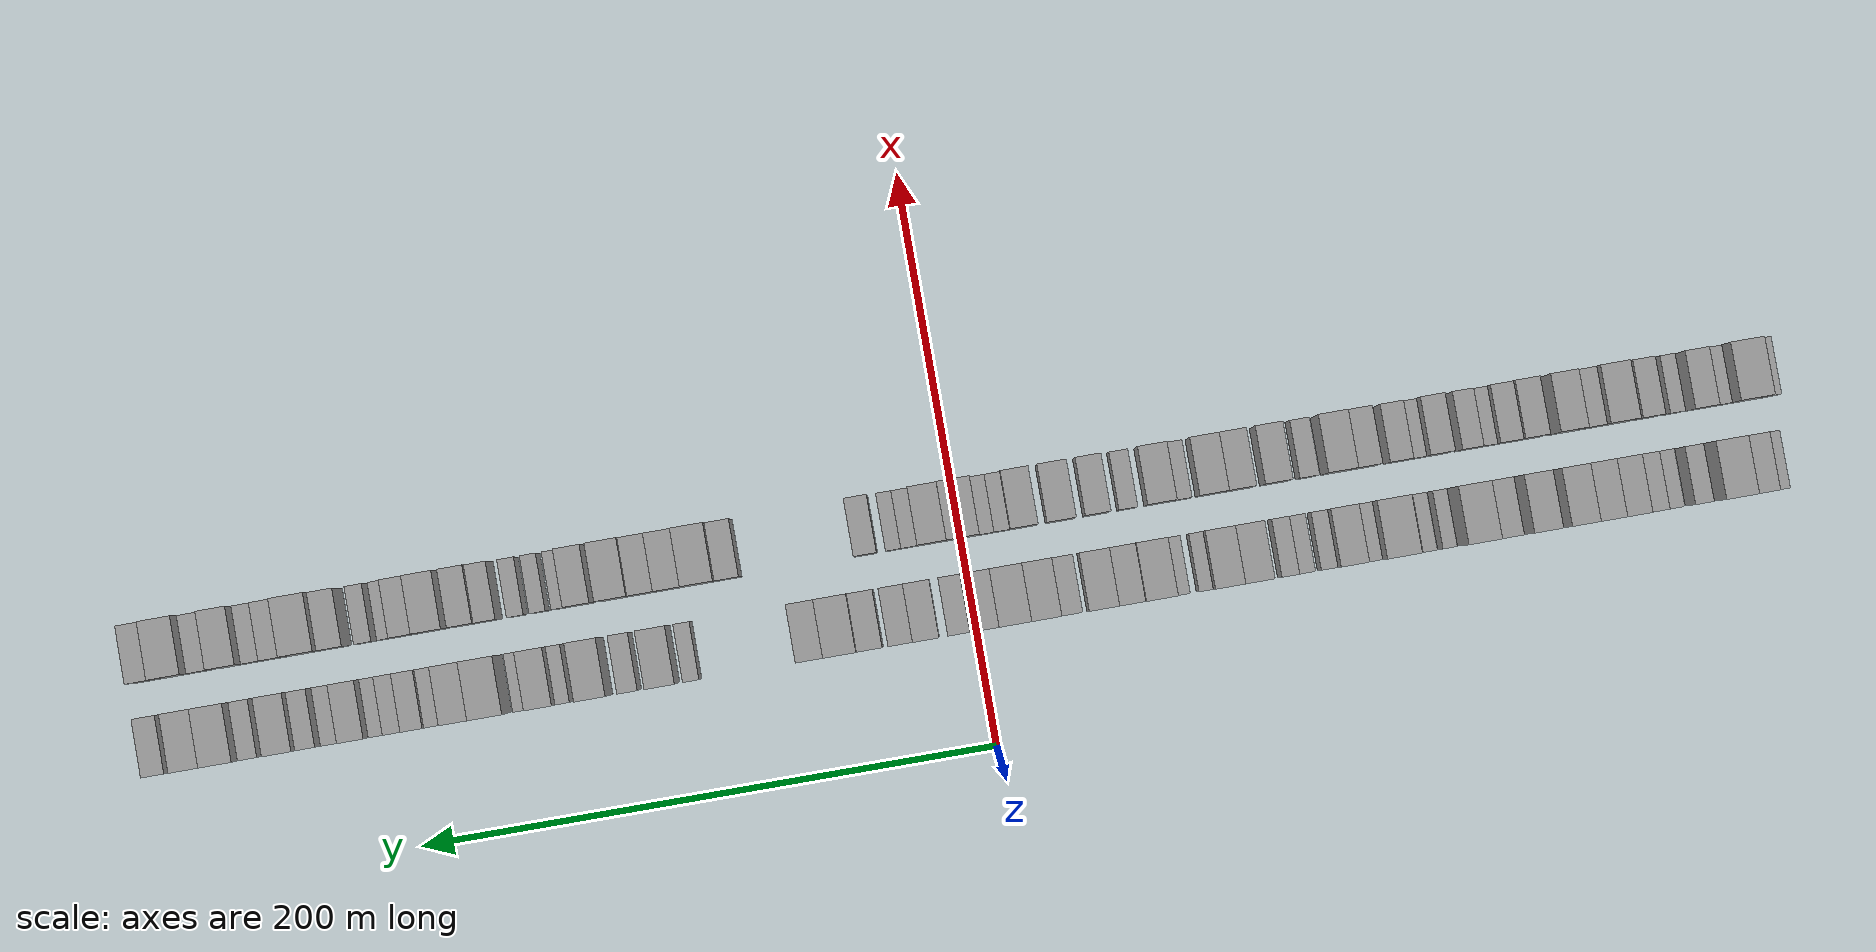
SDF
<sdf version="1.6">
 <world name="default">
  <scene>
   <sky><clouds><speed>12</speed></clouds></sky>
   <ambient>0.4 0.4 0.4 1</ambient>
   <background>0.7 0.7 0.7 1</background>
   <shadows>1</shadows>
  </scene>
  <gravity>0 0 -9.8066</gravity>
  <magnetic_field>6e-06 2.3e-05 -4.2e-05</magnetic_field>
  <physics default="0" name="default_physics" type="ode">
   <ode>
    <solver>
     <type>quick</type>
     <iters>10</iters>
     <sor>1.0</sor>
     <use_dynamic_moi_rescaling>0</use_dynamic_moi_rescaling>
    </solver>
    <constraints>
     <cfm>0</cfm>
     <erp>0.2</erp>
     <contact_max_correcting_vel>100</contact_max_correcting_vel>
     <contact_surface_layer>0.001</contact_surface_layer>
    </constraints>
   </ode>
   <max_step_size>0.004</max_step_size>
   <real_time_factor>1</real_time_factor>
   <real_time_update_rate>250</real_time_update_rate>
  </physics>
  <light name="sun" type="directional">
   <pose>0 0 10 0 0 0</pose>
   <diffuse>0.8 0.8 0.8 1</diffuse>
   <specular>0.2 0.2 0.2 1</specular>
   <attenuation>
    <range>1000</range>
    <constant>0.9</constant>
    <linear>0.01</linear>
    <quadratic>0.001</quadratic>
   </attenuation>
   <direction>-0.5 0.1 -0.9</direction>
  </light>
  <model name="building_1">
   <static>1</static>
   <pose>50.0000 -278.5065 0 0.000000 0.000000 0.000000</pose>
   <link name="link">
    <pose>0 0 6.00 0 0 0</pose>
    <collision name="collision"><geometry><box><size>20.0000 4.9871 12.0000</size></box></geometry></collision>
    <visual name="visual">
     <cast_shadows>0</cast_shadows>
     <geometry><box><size>20.0000 4.9871 12.0000</size></box></geometry>
     <material>
      <script>
       <uri>model://grey_wall/materials/scripts</uri>
       <uri>model://grey_wall/materials/textures</uri>
       <name>vrc/grey_wall</name>
      </script>
     </material>
    </visual>
   </link>
  </model>
  <model name="building_2">
   <static>1</static>
   <pose>50.0000 -271.5844 0 0.000000 0.000000 0.000000</pose>
   <link name="link">
    <pose>0 0 9.00 0 0 0</pose>
    <collision name="collision"><geometry><box><size>20.0000 8.8571 18.0000</size></box></geometry></collision>
    <visual name="visual">
     <cast_shadows>0</cast_shadows>
     <geometry><box><size>20.0000 8.8571 18.0000</size></box></geometry>
     <material>
      <script>
       <uri>model://grey_wall/materials/scripts</uri>
       <uri>model://grey_wall/materials/textures</uri>
       <name>vrc/grey_wall</name>
      </script>
     </material>
    </visual>
   </link>
  </model>
  <model name="building_3">
   <static>1</static>
   <pose>50.0000 -261.5366 0 0.000000 0.000000 0.000000</pose>
   <link name="link">
    <pose>0 0 12.00 0 0 0</pose>
    <collision name="collision"><geometry><box><size>20.0000 11.2384 24.0000</size></box></geometry></collision>
    <visual name="visual">
     <cast_shadows>0</cast_shadows>
     <geometry><box><size>20.0000 11.2384 24.0000</size></box></geometry>
     <material>
      <script>
       <uri>model://grey_wall/materials/scripts</uri>
       <uri>model://grey_wall/materials/textures</uri>
       <name>vrc/grey_wall</name>
      </script>
     </material>
    </visual>
   </link>
  </model>
  <model name="building_4">
   <static>1</static>
   <pose>50.0000 -250.6917 0 0.000000 0.000000 0.000000</pose>
   <link name="link">
    <pose>0 0 7.50 0 0 0</pose>
    <collision name="collision"><geometry><box><size>20.0000 6.4514 15.0000</size></box></geometry></collision>
    <visual name="visual">
     <cast_shadows>0</cast_shadows>
     <geometry><box><size>20.0000 6.4514 15.0000</size></box></geometry>
     <material>
      <script>
       <uri>model://grey_wall/materials/scripts</uri>
       <uri>model://grey_wall/materials/textures</uri>
       <name>vrc/grey_wall</name>
      </script>
     </material>
    </visual>
   </link>
  </model>
  <model name="building_5">
   <static>1</static>
   <pose>50.0000 -241.5731 0 0.000000 0.000000 0.000000</pose>
   <link name="link">
    <pose>0 0 6.00 0 0 0</pose>
    <collision name="collision"><geometry><box><size>20.0000 5.7857 12.0000</size></box></geometry></collision>
    <visual name="visual">
     <cast_shadows>0</cast_shadows>
     <geometry><box><size>20.0000 5.7857 12.0000</size></box></geometry>
     <material>
      <script>
       <uri>model://grey_wall/materials/scripts</uri>
       <uri>model://grey_wall/materials/textures</uri>
       <name>vrc/grey_wall</name>
      </script>
     </material>
    </visual>
   </link>
  </model>
  <model name="building_6">
   <static>1</static>
   <pose>50.0000 -235.0290 0 0.000000 0.000000 0.000000</pose>
   <link name="link">
    <pose>0 0 7.50 0 0 0</pose>
    <collision name="collision"><geometry><box><size>20.0000 7.3026 15.0000</size></box></geometry></collision>
    <visual name="visual">
     <cast_shadows>0</cast_shadows>
     <geometry><box><size>20.0000 7.3026 15.0000</size></box></geometry>
     <material>
      <script>
       <uri>model://grey_wall/materials/scripts</uri>
       <uri>model://grey_wall/materials/textures</uri>
       <name>vrc/grey_wall</name>
      </script>
     </material>
    </visual>
   </link>
  </model>
  <model name="building_7">
   <static>1</static>
   <pose>50.0000 -227.0505 0 0.000000 0.000000 0.000000</pose>
   <link name="link">
    <pose>0 0 10.50 0 0 0</pose>
    <collision name="collision"><geometry><box><size>20.0000 8.6544 21.0000</size></box></geometry></collision>
    <visual name="visual">
     <cast_shadows>0</cast_shadows>
     <geometry><box><size>20.0000 8.6544 21.0000</size></box></geometry>
     <material>
      <script>
       <uri>model://grey_wall/materials/scripts</uri>
       <uri>model://grey_wall/materials/textures</uri>
       <name>vrc/grey_wall</name>
      </script>
     </material>
    </visual>
   </link>
  </model>
  <model name="building_8">
   <static>1</static>
   <pose>50.0000 -218.1994 0 0.000000 0.000000 0.000000</pose>
   <link name="link">
    <pose>0 0 10.50 0 0 0</pose>
    <collision name="collision"><geometry><box><size>20.0000 9.0477 21.0000</size></box></geometry></collision>
    <visual name="visual">
     <cast_shadows>0</cast_shadows>
     <geometry><box><size>20.0000 9.0477 21.0000</size></box></geometry>
     <material>
      <script>
       <uri>model://grey_wall/materials/scripts</uri>
       <uri>model://grey_wall/materials/textures</uri>
       <name>vrc/grey_wall</name>
      </script>
     </material>
    </visual>
   </link>
  </model>
  <model name="building_9">
   <static>1</static>
   <pose>50.0000 -208.7246 0 0.000000 0.000000 0.000000</pose>
   <link name="link">
    <pose>0 0 10.50 0 0 0</pose>
    <collision name="collision"><geometry><box><size>20.0000 9.9019 21.0000</size></box></geometry></collision>
    <visual name="visual">
     <cast_shadows>0</cast_shadows>
     <geometry><box><size>20.0000 9.9019 21.0000</size></box></geometry>
     <material>
      <script>
       <uri>model://grey_wall/materials/scripts</uri>
       <uri>model://grey_wall/materials/textures</uri>
       <name>vrc/grey_wall</name>
      </script>
     </material>
    </visual>
   </link>
  </model>
  <model name="building_10">
   <static>1</static>
   <pose>50.0000 -195.8048 0 0.000000 0.000000 0.000000</pose>
   <link name="link">
    <pose>0 0 10.50 0 0 0</pose>
    <collision name="collision"><geometry><box><size>20.0000 9.9379 21.0000</size></box></geometry></collision>
    <visual name="visual">
     <cast_shadows>0</cast_shadows>
     <geometry><box><size>20.0000 9.9379 21.0000</size></box></geometry>
     <material>
      <script>
       <uri>model://grey_wall/materials/scripts</uri>
       <uri>model://grey_wall/materials/textures</uri>
       <name>vrc/grey_wall</name>
      </script>
     </material>
    </visual>
   </link>
  </model>
  <model name="building_11">
   <static>1</static>
   <pose>50.0000 -183.5506 0 0.000000 0.000000 0.000000</pose>
   <link name="link">
    <pose>0 0 9.00 0 0 0</pose>
    <collision name="collision"><geometry><box><size>20.0000 8.5705 18.0000</size></box></geometry></collision>
    <visual name="visual">
     <cast_shadows>0</cast_shadows>
     <geometry><box><size>20.0000 8.5705 18.0000</size></box></geometry>
     <material>
      <script>
       <uri>model://grey_wall/materials/scripts</uri>
       <uri>model://grey_wall/materials/textures</uri>
       <name>vrc/grey_wall</name>
      </script>
     </material>
    </visual>
   </link>
  </model>
  <model name="building_12">
   <static>1</static>
   <pose>50.0000 -173.5130 0 0.000000 0.000000 0.000000</pose>
   <link name="link">
    <pose>0 0 12.00 0 0 0</pose>
    <collision name="collision"><geometry><box><size>20.0000 11.5047 24.0000</size></box></geometry></collision>
    <visual name="visual">
     <cast_shadows>0</cast_shadows>
     <geometry><box><size>20.0000 11.5047 24.0000</size></box></geometry>
     <material>
      <script>
       <uri>model://grey_wall/materials/scripts</uri>
       <uri>model://grey_wall/materials/textures</uri>
       <name>vrc/grey_wall</name>
      </script>
     </material>
    </visual>
   </link>
  </model>
  <model name="building_13">
   <static>1</static>
   <pose>50.0000 -163.2944 0 0.000000 0.000000 0.000000</pose>
   <link name="link">
    <pose>0 0 6.00 0 0 0</pose>
    <collision name="collision"><geometry><box><size>20.0000 4.9323 12.0000</size></box></geometry></collision>
    <visual name="visual">
     <cast_shadows>0</cast_shadows>
     <geometry><box><size>20.0000 4.9323 12.0000</size></box></geometry>
     <material>
      <script>
       <uri>model://grey_wall/materials/scripts</uri>
       <uri>model://grey_wall/materials/textures</uri>
       <name>vrc/grey_wall</name>
      </script>
     </material>
    </visual>
   </link>
  </model>
  <model name="building_14">
   <static>1</static>
   <pose>50.0000 -156.3599 0 0.000000 0.000000 0.000000</pose>
   <link name="link">
    <pose>0 0 6.00 0 0 0</pose>
    <collision name="collision"><geometry><box><size>20.0000 4.9368 12.0000</size></box></geometry></collision>
    <visual name="visual">
     <cast_shadows>0</cast_shadows>
     <geometry><box><size>20.0000 4.9368 12.0000</size></box></geometry>
     <material>
      <script>
       <uri>model://grey_wall/materials/scripts</uri>
       <uri>model://grey_wall/materials/textures</uri>
       <name>vrc/grey_wall</name>
      </script>
     </material>
    </visual>
   </link>
  </model>
  <model name="building_15">
   <static>1</static>
   <pose>50.0000 -145.9260 0 0.000000 0.000000 0.000000</pose>
   <link name="link">
    <pose>0 0 12.00 0 0 0</pose>
    <collision name="collision"><geometry><box><size>20.0000 11.9310 24.0000</size></box></geometry></collision>
    <visual name="visual">
     <cast_shadows>0</cast_shadows>
     <geometry><box><size>20.0000 11.9310 24.0000</size></box></geometry>
     <material>
      <script>
       <uri>model://grey_wall/materials/scripts</uri>
       <uri>model://grey_wall/materials/textures</uri>
       <name>vrc/grey_wall</name>
      </script>
     </material>
    </visual>
   </link>
  </model>
  <model name="building_16">
   <static>1</static>
   <pose>50.0000 -137.0980 0 0.000000 0.000000 0.000000</pose>
   <link name="link">
    <pose>0 0 6.00 0 0 0</pose>
    <collision name="collision"><geometry><box><size>20.0000 5.7249 12.0000</size></box></geometry></collision>
    <visual name="visual">
     <cast_shadows>0</cast_shadows>
     <geometry><box><size>20.0000 5.7249 12.0000</size></box></geometry>
     <material>
      <script>
       <uri>model://grey_wall/materials/scripts</uri>
       <uri>model://grey_wall/materials/textures</uri>
       <name>vrc/grey_wall</name>
      </script>
     </material>
    </visual>
   </link>
  </model>
  <model name="building_17">
   <static>1</static>
   <pose>50.0000 -129.3596 0 0.000000 0.000000 0.000000</pose>
   <link name="link">
    <pose>0 0 10.50 0 0 0</pose>
    <collision name="collision"><geometry><box><size>20.0000 9.7519 21.0000</size></box></geometry></collision>
    <visual name="visual">
     <cast_shadows>0</cast_shadows>
     <geometry><box><size>20.0000 9.7519 21.0000</size></box></geometry>
     <material>
      <script>
       <uri>model://grey_wall/materials/scripts</uri>
       <uri>model://grey_wall/materials/textures</uri>
       <name>vrc/grey_wall</name>
      </script>
     </material>
    </visual>
   </link>
  </model>
  <model name="building_18">
   <static>1</static>
   <pose>50.0000 -121.6277 0 0.000000 0.000000 0.000000</pose>
   <link name="link">
    <pose>0 0 6.00 0 0 0</pose>
    <collision name="collision"><geometry><box><size>20.0000 5.7120 12.0000</size></box></geometry></collision>
    <visual name="visual">
     <cast_shadows>0</cast_shadows>
     <geometry><box><size>20.0000 5.7120 12.0000</size></box></geometry>
     <material>
      <script>
       <uri>model://grey_wall/materials/scripts</uri>
       <uri>model://grey_wall/materials/textures</uri>
       <name>vrc/grey_wall</name>
      </script>
     </material>
    </visual>
   </link>
  </model>
  <model name="building_19">
   <static>1</static>
   <pose>50.0000 -113.8712 0 0.000000 0.000000 0.000000</pose>
   <link name="link">
    <pose>0 0 6.00 0 0 0</pose>
    <collision name="collision"><geometry><box><size>20.0000 5.8010 12.0000</size></box></geometry></collision>
    <visual name="visual">
     <cast_shadows>0</cast_shadows>
     <geometry><box><size>20.0000 5.8010 12.0000</size></box></geometry>
     <material>
      <script>
       <uri>model://grey_wall/materials/scripts</uri>
       <uri>model://grey_wall/materials/textures</uri>
       <name>vrc/grey_wall</name>
      </script>
     </material>
    </visual>
   </link>
  </model>
  <model name="building_20">
   <static>1</static>
   <pose>50.0000 -107.9117 0 0.000000 0.000000 0.000000</pose>
   <link name="link">
    <pose>0 0 7.50 0 0 0</pose>
    <collision name="collision"><geometry><box><size>20.0000 6.1179 15.0000</size></box></geometry></collision>
    <visual name="visual">
     <cast_shadows>0</cast_shadows>
     <geometry><box><size>20.0000 6.1179 15.0000</size></box></geometry>
     <material>
      <script>
       <uri>model://grey_wall/materials/scripts</uri>
       <uri>model://grey_wall/materials/textures</uri>
       <name>vrc/grey_wall</name>
      </script>
     </material>
    </visual>
   </link>
  </model>
  <model name="building_21">
   <static>1</static>
   <pose>50.0000 -96.8472 0 0.000000 0.000000 0.000000</pose>
   <link name="link">
    <pose>0 0 10.50 0 0 0</pose>
    <collision name="collision"><geometry><box><size>20.0000 10.0112 21.0000</size></box></geometry></collision>
    <visual name="visual">
     <cast_shadows>0</cast_shadows>
     <geometry><box><size>20.0000 10.0112 21.0000</size></box></geometry>
     <material>
      <script>
       <uri>model://grey_wall/materials/scripts</uri>
       <uri>model://grey_wall/materials/textures</uri>
       <name>vrc/grey_wall</name>
      </script>
     </material>
    </visual>
   </link>
  </model>
  <model name="building_22">
   <static>1</static>
   <pose>50.0000 -86.6377 0 0.000000 0.000000 0.000000</pose>
   <link name="link">
    <pose>0 0 10.50 0 0 0</pose>
    <collision name="collision"><geometry><box><size>20.0000 10.4077 21.0000</size></box></geometry></collision>
    <visual name="visual">
     <cast_shadows>0</cast_shadows>
     <geometry><box><size>20.0000 10.4077 21.0000</size></box></geometry>
     <material>
      <script>
       <uri>model://grey_wall/materials/scripts</uri>
       <uri>model://grey_wall/materials/textures</uri>
       <name>vrc/grey_wall</name>
      </script>
     </material>
    </visual>
   </link>
  </model>
  <model name="building_23">
   <static>1</static>
   <pose>50.0000 -78.9674 0 0.000000 0.000000 0.000000</pose>
   <link name="link">
    <pose>0 0 6.00 0 0 0</pose>
    <collision name="collision"><geometry><box><size>20.0000 4.9329 12.0000</size></box></geometry></collision>
    <visual name="visual">
     <cast_shadows>0</cast_shadows>
     <geometry><box><size>20.0000 4.9329 12.0000</size></box></geometry>
     <material>
      <script>
       <uri>model://grey_wall/materials/scripts</uri>
       <uri>model://grey_wall/materials/textures</uri>
       <name>vrc/grey_wall</name>
      </script>
     </material>
    </visual>
   </link>
  </model>
  <model name="building_24">
   <static>1</static>
   <pose>50.0000 -71.0161 0 0.000000 0.000000 0.000000</pose>
   <link name="link">
    <pose>0 0 6.00 0 0 0</pose>
    <collision name="collision"><geometry><box><size>20.0000 4.9698 12.0000</size></box></geometry></collision>
    <visual name="visual">
     <cast_shadows>0</cast_shadows>
     <geometry><box><size>20.0000 4.9698 12.0000</size></box></geometry>
     <material>
      <script>
       <uri>model://grey_wall/materials/scripts</uri>
       <uri>model://grey_wall/materials/textures</uri>
       <name>vrc/grey_wall</name>
      </script>
     </material>
    </visual>
   </link>
  </model>
  <model name="building_25">
   <static>1</static>
   <pose>50.0000 -63.0694 0 0.000000 0.000000 0.000000</pose>
   <link name="link">
    <pose>0 0 12.00 0 0 0</pose>
    <collision name="collision"><geometry><box><size>20.0000 10.9234 24.0000</size></box></geometry></collision>
    <visual name="visual">
     <cast_shadows>0</cast_shadows>
     <geometry><box><size>20.0000 10.9234 24.0000</size></box></geometry>
     <material>
      <script>
       <uri>model://grey_wall/materials/scripts</uri>
       <uri>model://grey_wall/materials/textures</uri>
       <name>vrc/grey_wall</name>
      </script>
     </material>
    </visual>
   </link>
  </model>
  <model name="building_26">
   <static>1</static>
   <pose>50.0000 -53.1333 0 0.000000 0.000000 0.000000</pose>
   <link name="link">
    <pose>0 0 10.50 0 0 0</pose>
    <collision name="collision"><geometry><box><size>20.0000 8.9490 21.0000</size></box></geometry></collision>
    <visual name="visual">
     <cast_shadows>0</cast_shadows>
     <geometry><box><size>20.0000 8.9490 21.0000</size></box></geometry>
     <material>
      <script>
       <uri>model://grey_wall/materials/scripts</uri>
       <uri>model://grey_wall/materials/textures</uri>
       <name>vrc/grey_wall</name>
      </script>
     </material>
    </visual>
   </link>
  </model>
  <model name="building_27">
   <static>1</static>
   <pose>50.0000 -43.4599 0 0.000000 0.000000 0.000000</pose>
   <link name="link">
    <pose>0 0 10.50 0 0 0</pose>
    <collision name="collision"><geometry><box><size>20.0000 10.3978 21.0000</size></box></geometry></collision>
    <visual name="visual">
     <cast_shadows>0</cast_shadows>
     <geometry><box><size>20.0000 10.3978 21.0000</size></box></geometry>
     <material>
      <script>
       <uri>model://grey_wall/materials/scripts</uri>
       <uri>model://grey_wall/materials/textures</uri>
       <name>vrc/grey_wall</name>
      </script>
     </material>
    </visual>
   </link>
  </model>
  <model name="building_28">
   <static>1</static>
   <pose>50.0000 -32.5189 0 0.000000 0.000000 0.000000</pose>
   <link name="link">
    <pose>0 0 7.50 0 0 0</pose>
    <collision name="collision"><geometry><box><size>20.0000 7.4841 15.0000</size></box></geometry></collision>
    <visual name="visual">
     <cast_shadows>0</cast_shadows>
     <geometry><box><size>20.0000 7.4841 15.0000</size></box></geometry>
     <material>
      <script>
       <uri>model://grey_wall/materials/scripts</uri>
       <uri>model://grey_wall/materials/textures</uri>
       <name>vrc/grey_wall</name>
      </script>
     </material>
    </visual>
   </link>
  </model>
  <model name="building_29">
   <static>1</static>
   <pose>50.0000 -23.6530 0 0.000000 0.000000 0.000000</pose>
   <link name="link">
    <pose>0 0 12.00 0 0 0</pose>
    <collision name="collision"><geometry><box><size>20.0000 10.2476 24.0000</size></box></geometry></collision>
    <visual name="visual">
     <cast_shadows>0</cast_shadows>
     <geometry><box><size>20.0000 10.2476 24.0000</size></box></geometry>
     <material>
      <script>
       <uri>model://grey_wall/materials/scripts</uri>
       <uri>model://grey_wall/materials/textures</uri>
       <name>vrc/grey_wall</name>
      </script>
     </material>
    </visual>
   </link>
  </model>
  <model name="building_30">
   <static>1</static>
   <pose>50.0000 -12.9464 0 0.000000 0.000000 0.000000</pose>
   <link name="link">
    <pose>0 0 12.00 0 0 0</pose>
    <collision name="collision"><geometry><box><size>20.0000 11.1657 24.0000</size></box></geometry></collision>
    <visual name="visual">
     <cast_shadows>0</cast_shadows>
     <geometry><box><size>20.0000 11.1657 24.0000</size></box></geometry>
     <material>
      <script>
       <uri>model://grey_wall/materials/scripts</uri>
       <uri>model://grey_wall/materials/textures</uri>
       <name>vrc/grey_wall</name>
      </script>
     </material>
    </visual>
   </link>
  </model>
  <model name="building_31">
   <static>1</static>
   <pose>50.0000 -2.3868 0 0.000000 0.000000 0.000000</pose>
   <link name="link">
    <pose>0 0 12.00 0 0 0</pose>
    <collision name="collision"><geometry><box><size>20.0000 9.9533 24.0000</size></box></geometry></collision>
    <visual name="visual">
     <cast_shadows>0</cast_shadows>
     <geometry><box><size>20.0000 9.9533 24.0000</size></box></geometry>
     <material>
      <script>
       <uri>model://grey_wall/materials/scripts</uri>
       <uri>model://grey_wall/materials/textures</uri>
       <name>vrc/grey_wall</name>
      </script>
     </material>
    </visual>
   </link>
  </model>
  <model name="building_32">
   <static>1</static>
   <pose>50.0000 6.3750 0 0.000000 0.000000 0.000000</pose>
   <link name="link">
    <pose>0 0 9.00 0 0 0</pose>
    <collision name="collision"><geometry><box><size>20.0000 7.5704 18.0000</size></box></geometry></collision>
    <visual name="visual">
     <cast_shadows>0</cast_shadows>
     <geometry><box><size>20.0000 7.5704 18.0000</size></box></geometry>
     <material>
      <script>
       <uri>model://grey_wall/materials/scripts</uri>
       <uri>model://grey_wall/materials/textures</uri>
       <name>vrc/grey_wall</name>
      </script>
     </material>
    </visual>
   </link>
  </model>
  <model name="building_33">
   <static>1</static>
   <pose>50.0000 17.7057 0 0.000000 0.000000 0.000000</pose>
   <link name="link">
    <pose>0 0 10.50 0 0 0</pose>
    <collision name="collision"><geometry><box><size>20.0000 9.0910 21.0000</size></box></geometry></collision>
    <visual name="visual">
     <cast_shadows>0</cast_shadows>
     <geometry><box><size>20.0000 9.0910 21.0000</size></box></geometry>
     <material>
      <script>
       <uri>model://grey_wall/materials/scripts</uri>
       <uri>model://grey_wall/materials/textures</uri>
       <name>vrc/grey_wall</name>
      </script>
     </material>
    </visual>
   </link>
  </model>
  <model name="building_34">
   <static>1</static>
   <pose>50.0000 26.4657 0 0.000000 0.000000 0.000000</pose>
   <link name="link">
    <pose>0 0 9.00 0 0 0</pose>
    <collision name="collision"><geometry><box><size>20.0000 8.4290 18.0000</size></box></geometry></collision>
    <visual name="visual">
     <cast_shadows>0</cast_shadows>
     <geometry><box><size>20.0000 8.4290 18.0000</size></box></geometry>
     <material>
      <script>
       <uri>model://grey_wall/materials/scripts</uri>
       <uri>model://grey_wall/materials/textures</uri>
       <name>vrc/grey_wall</name>
      </script>
     </material>
    </visual>
   </link>
  </model>
  <model name="building_35">
   <static>1</static>
   <pose>50.0000 37.0979 0 0.000000 0.000000 0.000000</pose>
   <link name="link">
    <pose>0 0 9.00 0 0 0</pose>
    <collision name="collision"><geometry><box><size>20.0000 8.8355 18.0000</size></box></geometry></collision>
    <visual name="visual">
     <cast_shadows>0</cast_shadows>
     <geometry><box><size>20.0000 8.8355 18.0000</size></box></geometry>
     <material>
      <script>
       <uri>model://grey_wall/materials/scripts</uri>
       <uri>model://grey_wall/materials/textures</uri>
       <name>vrc/grey_wall</name>
      </script>
     </material>
    </visual>
   </link>
  </model>
  <model name="building_36">
   <static>1</static>
   <pose>50.0000 47.1653 0 0.000000 0.000000 0.000000</pose>
   <link name="link">
    <pose>0 0 12.00 0 0 0</pose>
    <collision name="collision"><geometry><box><size>20.0000 11.2991 24.0000</size></box></geometry></collision>
    <visual name="visual">
     <cast_shadows>0</cast_shadows>
     <geometry><box><size>20.0000 11.2991 24.0000</size></box></geometry>
     <material>
      <script>
       <uri>model://grey_wall/materials/scripts</uri>
       <uri>model://grey_wall/materials/textures</uri>
       <name>vrc/grey_wall</name>
      </script>
     </material>
    </visual>
   </link>
  </model>
  <model name="building_37">
   <static>1</static>
   <pose>50.0000 57.5591 0 0.000000 0.000000 0.000000</pose>
   <link name="link">
    <pose>0 0 10.50 0 0 0</pose>
    <collision name="collision"><geometry><box><size>20.0000 9.4886 21.0000</size></box></geometry></collision>
    <visual name="visual">
     <cast_shadows>0</cast_shadows>
     <geometry><box><size>20.0000 9.4886 21.0000</size></box></geometry>
     <material>
      <script>
       <uri>model://grey_wall/materials/scripts</uri>
       <uri>model://grey_wall/materials/textures</uri>
       <name>vrc/grey_wall</name>
      </script>
     </material>
    </visual>
   </link>
  </model>
  <model name="building_38">
   <static>1</static>
   <pose>50.0000 98.7756 0 0.000000 0.000000 0.000000</pose>
   <link name="link">
    <pose>0 0 6.00 0 0 0</pose>
    <collision name="collision"><geometry><box><size>20.0000 5.6481 12.0000</size></box></geometry></collision>
    <visual name="visual">
     <cast_shadows>0</cast_shadows>
     <geometry><box><size>20.0000 5.6481 12.0000</size></box></geometry>
     <material>
      <script>
       <uri>model://grey_wall/materials/scripts</uri>
       <uri>model://grey_wall/materials/textures</uri>
       <name>vrc/grey_wall</name>
      </script>
     </material>
    </visual>
   </link>
  </model>
  <model name="building_39">
   <static>1</static>
   <pose>50.0000 108.7570 0 0.000000 0.000000 0.000000</pose>
   <link name="link">
    <pose>0 0 10.50 0 0 0</pose>
    <collision name="collision"><geometry><box><size>20.0000 10.3148 21.0000</size></box></geometry></collision>
    <visual name="visual">
     <cast_shadows>0</cast_shadows>
     <geometry><box><size>20.0000 10.3148 21.0000</size></box></geometry>
     <material>
      <script>
       <uri>model://grey_wall/materials/scripts</uri>
       <uri>model://grey_wall/materials/textures</uri>
       <name>vrc/grey_wall</name>
      </script>
     </material>
    </visual>
   </link>
  </model>
  <model name="building_40">
   <static>1</static>
   <pose>50.0000 120.3956 0 0.000000 0.000000 0.000000</pose>
   <link name="link">
    <pose>0 0 7.50 0 0 0</pose>
    <collision name="collision"><geometry><box><size>20.0000 6.9623 15.0000</size></box></geometry></collision>
    <visual name="visual">
     <cast_shadows>0</cast_shadows>
     <geometry><box><size>20.0000 6.9623 15.0000</size></box></geometry>
     <material>
      <script>
       <uri>model://grey_wall/materials/scripts</uri>
       <uri>model://grey_wall/materials/textures</uri>
       <name>vrc/grey_wall</name>
      </script>
     </material>
    </visual>
   </link>
  </model>
  <model name="building_41">
   <static>1</static>
   <pose>50.0000 132.2311 0 0.000000 0.000000 0.000000</pose>
   <link name="link">
    <pose>0 0 12.00 0 0 0</pose>
    <collision name="collision"><geometry><box><size>20.0000 10.7086 24.0000</size></box></geometry></collision>
    <visual name="visual">
     <cast_shadows>0</cast_shadows>
     <geometry><box><size>20.0000 10.7086 24.0000</size></box></geometry>
     <material>
      <script>
       <uri>model://grey_wall/materials/scripts</uri>
       <uri>model://grey_wall/materials/textures</uri>
       <name>vrc/grey_wall</name>
      </script>
     </material>
    </visual>
   </link>
  </model>
  <model name="building_42">
   <static>1</static>
   <pose>50.0000 143.0597 0 0.000000 0.000000 0.000000</pose>
   <link name="link">
    <pose>0 0 6.00 0 0 0</pose>
    <collision name="collision"><geometry><box><size>20.0000 4.9486 12.0000</size></box></geometry></collision>
    <visual name="visual">
     <cast_shadows>0</cast_shadows>
     <geometry><box><size>20.0000 4.9486 12.0000</size></box></geometry>
     <material>
      <script>
       <uri>model://grey_wall/materials/scripts</uri>
       <uri>model://grey_wall/materials/textures</uri>
       <name>vrc/grey_wall</name>
      </script>
     </material>
    </visual>
   </link>
  </model>
  <model name="building_43">
   <static>1</static>
   <pose>50.0000 150.3219 0 0.000000 0.000000 0.000000</pose>
   <link name="link">
    <pose>0 0 10.50 0 0 0</pose>
    <collision name="collision"><geometry><box><size>20.0000 9.5759 21.0000</size></box></geometry></collision>
    <visual name="visual">
     <cast_shadows>0</cast_shadows>
     <geometry><box><size>20.0000 9.5759 21.0000</size></box></geometry>
     <material>
      <script>
       <uri>model://grey_wall/materials/scripts</uri>
       <uri>model://grey_wall/materials/textures</uri>
       <name>vrc/grey_wall</name>
      </script>
     </material>
    </visual>
   </link>
  </model>
  <model name="building_44">
   <static>1</static>
   <pose>50.0000 157.5859 0 0.000000 0.000000 0.000000</pose>
   <link name="link">
    <pose>0 0 6.00 0 0 0</pose>
    <collision name="collision"><geometry><box><size>20.0000 4.9522 12.0000</size></box></geometry></collision>
    <visual name="visual">
     <cast_shadows>0</cast_shadows>
     <geometry><box><size>20.0000 4.9522 12.0000</size></box></geometry>
     <material>
      <script>
       <uri>model://grey_wall/materials/scripts</uri>
       <uri>model://grey_wall/materials/textures</uri>
       <name>vrc/grey_wall</name>
      </script>
     </material>
    </visual>
   </link>
  </model>
  <model name="building_45">
   <static>1</static>
   <pose>50.0000 168.0067 0 0.000000 0.000000 0.000000</pose>
   <link name="link">
    <pose>0 0 12.00 0 0 0</pose>
    <collision name="collision"><geometry><box><size>20.0000 11.8894 24.0000</size></box></geometry></collision>
    <visual name="visual">
     <cast_shadows>0</cast_shadows>
     <geometry><box><size>20.0000 11.8894 24.0000</size></box></geometry>
     <material>
      <script>
       <uri>model://grey_wall/materials/scripts</uri>
       <uri>model://grey_wall/materials/textures</uri>
       <name>vrc/grey_wall</name>
      </script>
     </material>
    </visual>
   </link>
  </model>
  <model name="building_46">
   <static>1</static>
   <pose>50.0000 179.0463 0 0.000000 0.000000 0.000000</pose>
   <link name="link">
    <pose>0 0 10.50 0 0 0</pose>
    <collision name="collision"><geometry><box><size>20.0000 10.1898 21.0000</size></box></geometry></collision>
    <visual name="visual">
     <cast_shadows>0</cast_shadows>
     <geometry><box><size>20.0000 10.1898 21.0000</size></box></geometry>
     <material>
      <script>
       <uri>model://grey_wall/materials/scripts</uri>
       <uri>model://grey_wall/materials/textures</uri>
       <name>vrc/grey_wall</name>
      </script>
     </material>
    </visual>
   </link>
  </model>
  <model name="building_47">
   <static>1</static>
   <pose>50.0000 187.1726 0 0.000000 0.000000 0.000000</pose>
   <link name="link">
    <pose>0 0 7.50 0 0 0</pose>
    <collision name="collision"><geometry><box><size>20.0000 6.0628 15.0000</size></box></geometry></collision>
    <visual name="visual">
     <cast_shadows>0</cast_shadows>
     <geometry><box><size>20.0000 6.0628 15.0000</size></box></geometry>
     <material>
      <script>
       <uri>model://grey_wall/materials/scripts</uri>
       <uri>model://grey_wall/materials/textures</uri>
       <name>vrc/grey_wall</name>
      </script>
     </material>
    </visual>
   </link>
  </model>
  <model name="building_48">
   <static>1</static>
   <pose>50.0000 193.9692 0 0.000000 0.000000 0.000000</pose>
   <link name="link">
    <pose>0 0 9.00 0 0 0</pose>
    <collision name="collision"><geometry><box><size>20.0000 7.5304 18.0000</size></box></geometry></collision>
    <visual name="visual">
     <cast_shadows>0</cast_shadows>
     <geometry><box><size>20.0000 7.5304 18.0000</size></box></geometry>
     <material>
      <script>
       <uri>model://grey_wall/materials/scripts</uri>
       <uri>model://grey_wall/materials/textures</uri>
       <name>vrc/grey_wall</name>
      </script>
     </material>
    </visual>
   </link>
  </model>
  <model name="building_49">
   <static>1</static>
   <pose>50.0000 201.0462 0 0.000000 0.000000 0.000000</pose>
   <link name="link">
    <pose>0 0 7.50 0 0 0</pose>
    <collision name="collision"><geometry><box><size>20.0000 6.6235 15.0000</size></box></geometry></collision>
    <visual name="visual">
     <cast_shadows>0</cast_shadows>
     <geometry><box><size>20.0000 6.6235 15.0000</size></box></geometry>
     <material>
      <script>
       <uri>model://grey_wall/materials/scripts</uri>
       <uri>model://grey_wall/materials/textures</uri>
       <name>vrc/grey_wall</name>
      </script>
     </material>
    </visual>
   </link>
  </model>
  <model name="building_50">
   <static>1</static>
   <pose>50.0000 207.0693 0 0.000000 0.000000 0.000000</pose>
   <link name="link">
    <pose>0 0 6.00 0 0 0</pose>
    <collision name="collision"><geometry><box><size>20.0000 5.4227 12.0000</size></box></geometry></collision>
    <visual name="visual">
     <cast_shadows>0</cast_shadows>
     <geometry><box><size>20.0000 5.4227 12.0000</size></box></geometry>
     <material>
      <script>
       <uri>model://grey_wall/materials/scripts</uri>
       <uri>model://grey_wall/materials/textures</uri>
       <name>vrc/grey_wall</name>
      </script>
     </material>
    </visual>
   </link>
  </model>
  <model name="building_51">
   <static>1</static>
   <pose>50.0000 214.3132 0 0.000000 0.000000 0.000000</pose>
   <link name="link">
    <pose>0 0 10.50 0 0 0</pose>
    <collision name="collision"><geometry><box><size>20.0000 9.0652 21.0000</size></box></geometry></collision>
    <visual name="visual">
     <cast_shadows>0</cast_shadows>
     <geometry><box><size>20.0000 9.0652 21.0000</size></box></geometry>
     <material>
      <script>
       <uri>model://grey_wall/materials/scripts</uri>
       <uri>model://grey_wall/materials/textures</uri>
       <name>vrc/grey_wall</name>
      </script>
     </material>
    </visual>
   </link>
  </model>
  <model name="building_52">
   <static>1</static>
   <pose>50.0000 222.1941 0 0.000000 0.000000 0.000000</pose>
   <link name="link">
    <pose>0 0 7.50 0 0 0</pose>
    <collision name="collision"><geometry><box><size>20.0000 6.6967 15.0000</size></box></geometry></collision>
    <visual name="visual">
     <cast_shadows>0</cast_shadows>
     <geometry><box><size>20.0000 6.6967 15.0000</size></box></geometry>
     <material>
      <script>
       <uri>model://grey_wall/materials/scripts</uri>
       <uri>model://grey_wall/materials/textures</uri>
       <name>vrc/grey_wall</name>
      </script>
     </material>
    </visual>
   </link>
  </model>
  <model name="building_53">
   <static>1</static>
   <pose>50.0000 230.9654 0 0.000000 0.000000 0.000000</pose>
   <link name="link">
    <pose>0 0 7.50 0 0 0</pose>
    <collision name="collision"><geometry><box><size>20.0000 6.8459 15.0000</size></box></geometry></collision>
    <visual name="visual">
     <cast_shadows>0</cast_shadows>
     <geometry><box><size>20.0000 6.8459 15.0000</size></box></geometry>
     <material>
      <script>
       <uri>model://grey_wall/materials/scripts</uri>
       <uri>model://grey_wall/materials/textures</uri>
       <name>vrc/grey_wall</name>
      </script>
     </material>
    </visual>
   </link>
  </model>
  <model name="building_54">
   <static>1</static>
   <pose>50.0000 239.3948 0 0.000000 0.000000 0.000000</pose>
   <link name="link">
    <pose>0 0 10.50 0 0 0</pose>
    <collision name="collision"><geometry><box><size>20.0000 10.0129 21.0000</size></box></geometry></collision>
    <visual name="visual">
     <cast_shadows>0</cast_shadows>
     <geometry><box><size>20.0000 10.0129 21.0000</size></box></geometry>
     <material>
      <script>
       <uri>model://grey_wall/materials/scripts</uri>
       <uri>model://grey_wall/materials/textures</uri>
       <name>vrc/grey_wall</name>
      </script>
     </material>
    </visual>
   </link>
  </model>
  <model name="building_55">
   <static>1</static>
   <pose>50.0000 250.7144 0 0.000000 0.000000 0.000000</pose>
   <link name="link">
    <pose>0 0 7.50 0 0 0</pose>
    <collision name="collision"><geometry><box><size>20.0000 6.6265 15.0000</size></box></geometry></collision>
    <visual name="visual">
     <cast_shadows>0</cast_shadows>
     <geometry><box><size>20.0000 6.6265 15.0000</size></box></geometry>
     <material>
      <script>
       <uri>model://grey_wall/materials/scripts</uri>
       <uri>model://grey_wall/materials/textures</uri>
       <name>vrc/grey_wall</name>
      </script>
     </material>
    </visual>
   </link>
  </model>
  <model name="building_56">
   <static>1</static>
   <pose>50.0000 259.6921 0 0.000000 0.000000 0.000000</pose>
   <link name="link">
    <pose>0 0 12.00 0 0 0</pose>
    <collision name="collision"><geometry><box><size>20.0000 11.3289 24.0000</size></box></geometry></collision>
    <visual name="visual">
     <cast_shadows>0</cast_shadows>
     <geometry><box><size>20.0000 11.3289 24.0000</size></box></geometry>
     <material>
      <script>
       <uri>model://grey_wall/materials/scripts</uri>
       <uri>model://grey_wall/materials/textures</uri>
       <name>vrc/grey_wall</name>
      </script>
     </material>
    </visual>
   </link>
  </model>
  <model name="building_57">
   <static>1</static>
   <pose>50.0000 270.4050 0 0.000000 0.000000 0.000000</pose>
   <link name="link">
    <pose>0 0 12.00 0 0 0</pose>
    <collision name="collision"><geometry><box><size>20.0000 10.0969 24.0000</size></box></geometry></collision>
    <visual name="visual">
     <cast_shadows>0</cast_shadows>
     <geometry><box><size>20.0000 10.0969 24.0000</size></box></geometry>
     <material>
      <script>
       <uri>model://grey_wall/materials/scripts</uri>
       <uri>model://grey_wall/materials/textures</uri>
       <name>vrc/grey_wall</name>
      </script>
     </material>
    </visual>
   </link>
  </model>
  <model name="building_58">
   <static>1</static>
   <pose>50.0000 282.4318 0 0.000000 0.000000 0.000000</pose>
   <link name="link">
    <pose>0 0 9.00 0 0 0</pose>
    <collision name="collision"><geometry><box><size>20.0000 7.9568 18.0000</size></box></geometry></collision>
    <visual name="visual">
     <cast_shadows>0</cast_shadows>
     <geometry><box><size>20.0000 7.9568 18.0000</size></box></geometry>
     <material>
      <script>
       <uri>model://grey_wall/materials/scripts</uri>
       <uri>model://grey_wall/materials/textures</uri>
       <name>vrc/grey_wall</name>
      </script>
     </material>
    </visual>
   </link>
  </model>
  <model name="building_59">
   <static>1</static>
   <pose>82.0000 -281.2946 0 0.000000 0.000000 0.000000</pose>
   <link name="link">
    <pose>0 0 6.00 0 0 0</pose>
    <collision name="collision"><geometry><box><size>20.0000 5.4108 12.0000</size></box></geometry></collision>
    <visual name="visual">
     <cast_shadows>0</cast_shadows>
     <geometry><box><size>20.0000 5.4108 12.0000</size></box></geometry>
     <material>
      <script>
       <uri>model://grey_wall/materials/scripts</uri>
       <uri>model://grey_wall/materials/textures</uri>
       <name>vrc/grey_wall</name>
      </script>
     </material>
    </visual>
   </link>
  </model>
  <model name="building_60">
   <static>1</static>
   <pose>82.0000 -272.7439 0 0.000000 0.000000 0.000000</pose>
   <link name="link">
    <pose>0 0 12.00 0 0 0</pose>
    <collision name="collision"><geometry><box><size>20.0000 11.6908 24.0000</size></box></geometry></collision>
    <visual name="visual">
     <cast_shadows>0</cast_shadows>
     <geometry><box><size>20.0000 11.6908 24.0000</size></box></geometry>
     <material>
      <script>
       <uri>model://grey_wall/materials/scripts</uri>
       <uri>model://grey_wall/materials/textures</uri>
       <name>vrc/grey_wall</name>
      </script>
     </material>
    </visual>
   </link>
  </model>
  <model name="building_61">
   <static>1</static>
   <pose>82.0000 -264.0262 0 0.000000 0.000000 0.000000</pose>
   <link name="link">
    <pose>0 0 6.00 0 0 0</pose>
    <collision name="collision"><geometry><box><size>20.0000 5.7445 12.0000</size></box></geometry></collision>
    <visual name="visual">
     <cast_shadows>0</cast_shadows>
     <geometry><box><size>20.0000 5.7445 12.0000</size></box></geometry>
     <material>
      <script>
       <uri>model://grey_wall/materials/scripts</uri>
       <uri>model://grey_wall/materials/textures</uri>
       <name>vrc/grey_wall</name>
      </script>
     </material>
    </visual>
   </link>
  </model>
  <model name="building_62">
   <static>1</static>
   <pose>82.0000 -256.9357 0 0.000000 0.000000 0.000000</pose>
   <link name="link">
    <pose>0 0 9.00 0 0 0</pose>
    <collision name="collision"><geometry><box><size>20.0000 8.4366 18.0000</size></box></geometry></collision>
    <visual name="visual">
     <cast_shadows>0</cast_shadows>
     <geometry><box><size>20.0000 8.4366 18.0000</size></box></geometry>
     <material>
      <script>
       <uri>model://grey_wall/materials/scripts</uri>
       <uri>model://grey_wall/materials/textures</uri>
       <name>vrc/grey_wall</name>
      </script>
     </material>
    </visual>
   </link>
  </model>
  <model name="building_63">
   <static>1</static>
   <pose>82.0000 -248.0878 0 0.000000 0.000000 0.000000</pose>
   <link name="link">
    <pose>0 0 6.00 0 0 0</pose>
    <collision name="collision"><geometry><box><size>20.0000 5.2592 12.0000</size></box></geometry></collision>
    <visual name="visual">
     <cast_shadows>0</cast_shadows>
     <geometry><box><size>20.0000 5.2592 12.0000</size></box></geometry>
     <material>
      <script>
       <uri>model://grey_wall/materials/scripts</uri>
       <uri>model://grey_wall/materials/textures</uri>
       <name>vrc/grey_wall</name>
      </script>
     </material>
    </visual>
   </link>
  </model>
  <model name="building_64">
   <static>1</static>
   <pose>82.0000 -238.5676 0 0.000000 0.000000 0.000000</pose>
   <link name="link">
    <pose>0 0 9.00 0 0 0</pose>
    <collision name="collision"><geometry><box><size>20.0000 7.7812 18.0000</size></box></geometry></collision>
    <visual name="visual">
     <cast_shadows>0</cast_shadows>
     <geometry><box><size>20.0000 7.7812 18.0000</size></box></geometry>
     <material>
      <script>
       <uri>model://grey_wall/materials/scripts</uri>
       <uri>model://grey_wall/materials/textures</uri>
       <name>vrc/grey_wall</name>
      </script>
     </material>
    </visual>
   </link>
  </model>
  <model name="building_65">
   <static>1</static>
   <pose>82.0000 -227.4914 0 0.000000 0.000000 0.000000</pose>
   <link name="link">
    <pose>0 0 12.00 0 0 0</pose>
    <collision name="collision"><geometry><box><size>20.0000 10.3712 24.0000</size></box></geometry></collision>
    <visual name="visual">
     <cast_shadows>0</cast_shadows>
     <geometry><box><size>20.0000 10.3712 24.0000</size></box></geometry>
     <material>
      <script>
       <uri>model://grey_wall/materials/scripts</uri>
       <uri>model://grey_wall/materials/textures</uri>
       <name>vrc/grey_wall</name>
      </script>
     </material>
    </visual>
   </link>
  </model>
  <model name="building_66">
   <static>1</static>
   <pose>82.0000 -218.5998 0 0.000000 0.000000 0.000000</pose>
   <link name="link">
    <pose>0 0 9.00 0 0 0</pose>
    <collision name="collision"><geometry><box><size>20.0000 7.4120 18.0000</size></box></geometry></collision>
    <visual name="visual">
     <cast_shadows>0</cast_shadows>
     <geometry><box><size>20.0000 7.4120 18.0000</size></box></geometry>
     <material>
      <script>
       <uri>model://grey_wall/materials/scripts</uri>
       <uri>model://grey_wall/materials/textures</uri>
       <name>vrc/grey_wall</name>
      </script>
     </material>
    </visual>
   </link>
  </model>
  <model name="building_67">
   <static>1</static>
   <pose>82.0000 -210.0460 0 0.000000 0.000000 0.000000</pose>
   <link name="link">
    <pose>0 0 12.00 0 0 0</pose>
    <collision name="collision"><geometry><box><size>20.0000 9.6958 24.0000</size></box></geometry></collision>
    <visual name="visual">
     <cast_shadows>0</cast_shadows>
     <geometry><box><size>20.0000 9.6958 24.0000</size></box></geometry>
     <material>
      <script>
       <uri>model://grey_wall/materials/scripts</uri>
       <uri>model://grey_wall/materials/textures</uri>
       <name>vrc/grey_wall</name>
      </script>
     </material>
    </visual>
   </link>
  </model>
  <model name="building_68">
   <static>1</static>
   <pose>82.0000 -197.8975 0 0.000000 0.000000 0.000000</pose>
   <link name="link">
    <pose>0 0 10.50 0 0 0</pose>
    <collision name="collision"><geometry><box><size>20.0000 8.6012 21.0000</size></box></geometry></collision>
    <visual name="visual">
     <cast_shadows>0</cast_shadows>
     <geometry><box><size>20.0000 8.6012 21.0000</size></box></geometry>
     <material>
      <script>
       <uri>model://grey_wall/materials/scripts</uri>
       <uri>model://grey_wall/materials/textures</uri>
       <name>vrc/grey_wall</name>
      </script>
     </material>
    </visual>
   </link>
  </model>
  <model name="building_69">
   <static>1</static>
   <pose>82.0000 -189.6049 0 0.000000 0.000000 0.000000</pose>
   <link name="link">
    <pose>0 0 9.00 0 0 0</pose>
    <collision name="collision"><geometry><box><size>20.0000 7.9839 18.0000</size></box></geometry></collision>
    <visual name="visual">
     <cast_shadows>0</cast_shadows>
     <geometry><box><size>20.0000 7.9839 18.0000</size></box></geometry>
     <material>
      <script>
       <uri>model://grey_wall/materials/scripts</uri>
       <uri>model://grey_wall/materials/textures</uri>
       <name>vrc/grey_wall</name>
      </script>
     </material>
    </visual>
   </link>
  </model>
  <model name="building_70">
   <static>1</static>
   <pose>82.0000 -182.7330 0 0.000000 0.000000 0.000000</pose>
   <link name="link">
    <pose>0 0 6.00 0 0 0</pose>
    <collision name="collision"><geometry><box><size>20.0000 5.7600 12.0000</size></box></geometry></collision>
    <visual name="visual">
     <cast_shadows>0</cast_shadows>
     <geometry><box><size>20.0000 5.7600 12.0000</size></box></geometry>
     <material>
      <script>
       <uri>model://grey_wall/materials/scripts</uri>
       <uri>model://grey_wall/materials/textures</uri>
       <name>vrc/grey_wall</name>
      </script>
     </material>
    </visual>
   </link>
  </model>
  <model name="building_71">
   <static>1</static>
   <pose>82.0000 -176.1849 0 0.000000 0.000000 0.000000</pose>
   <link name="link">
    <pose>0 0 9.00 0 0 0</pose>
    <collision name="collision"><geometry><box><size>20.0000 7.3361 18.0000</size></box></geometry></collision>
    <visual name="visual">
     <cast_shadows>0</cast_shadows>
     <geometry><box><size>20.0000 7.3361 18.0000</size></box></geometry>
     <material>
      <script>
       <uri>model://grey_wall/materials/scripts</uri>
       <uri>model://grey_wall/materials/textures</uri>
       <name>vrc/grey_wall</name>
      </script>
     </material>
    </visual>
   </link>
  </model>
  <model name="building_72">
   <static>1</static>
   <pose>82.0000 -165.2779 0 0.000000 0.000000 0.000000</pose>
   <link name="link">
    <pose>0 0 10.50 0 0 0</pose>
    <collision name="collision"><geometry><box><size>20.0000 8.4780 21.0000</size></box></geometry></collision>
    <visual name="visual">
     <cast_shadows>0</cast_shadows>
     <geometry><box><size>20.0000 8.4780 21.0000</size></box></geometry>
     <material>
      <script>
       <uri>model://grey_wall/materials/scripts</uri>
       <uri>model://grey_wall/materials/textures</uri>
       <name>vrc/grey_wall</name>
      </script>
     </material>
    </visual>
   </link>
  </model>
  <model name="building_73">
   <static>1</static>
   <pose>82.0000 -158.3622 0 0.000000 0.000000 0.000000</pose>
   <link name="link">
    <pose>0 0 6.00 0 0 0</pose>
    <collision name="collision"><geometry><box><size>20.0000 5.3534 12.0000</size></box></geometry></collision>
    <visual name="visual">
     <cast_shadows>0</cast_shadows>
     <geometry><box><size>20.0000 5.3534 12.0000</size></box></geometry>
     <material>
      <script>
       <uri>model://grey_wall/materials/scripts</uri>
       <uri>model://grey_wall/materials/textures</uri>
       <name>vrc/grey_wall</name>
      </script>
     </material>
    </visual>
   </link>
  </model>
  <model name="building_74">
   <static>1</static>
   <pose>82.0000 -151.6427 0 0.000000 0.000000 0.000000</pose>
   <link name="link">
    <pose>0 0 9.00 0 0 0</pose>
    <collision name="collision"><geometry><box><size>20.0000 8.0855 18.0000</size></box></geometry></collision>
    <visual name="visual">
     <cast_shadows>0</cast_shadows>
     <geometry><box><size>20.0000 8.0855 18.0000</size></box></geometry>
     <material>
      <script>
       <uri>model://grey_wall/materials/scripts</uri>
       <uri>model://grey_wall/materials/textures</uri>
       <name>vrc/grey_wall</name>
      </script>
     </material>
    </visual>
   </link>
  </model>
  <model name="building_75">
   <static>1</static>
   <pose>82.0000 -140.2580 0 0.000000 0.000000 0.000000</pose>
   <link name="link">
    <pose>0 0 10.50 0 0 0</pose>
    <collision name="collision"><geometry><box><size>20.0000 8.6839 21.0000</size></box></geometry></collision>
    <visual name="visual">
     <cast_shadows>0</cast_shadows>
     <geometry><box><size>20.0000 8.6839 21.0000</size></box></geometry>
     <material>
      <script>
       <uri>model://grey_wall/materials/scripts</uri>
       <uri>model://grey_wall/materials/textures</uri>
       <name>vrc/grey_wall</name>
      </script>
     </material>
    </visual>
   </link>
  </model>
  <model name="building_76">
   <static>1</static>
   <pose>82.0000 -130.7695 0 0.000000 0.000000 0.000000</pose>
   <link name="link">
    <pose>0 0 12.00 0 0 0</pose>
    <collision name="collision"><geometry><box><size>20.0000 10.2931 24.0000</size></box></geometry></collision>
    <visual name="visual">
     <cast_shadows>0</cast_shadows>
     <geometry><box><size>20.0000 10.2931 24.0000</size></box></geometry>
     <material>
      <script>
       <uri>model://grey_wall/materials/scripts</uri>
       <uri>model://grey_wall/materials/textures</uri>
       <name>vrc/grey_wall</name>
      </script>
     </material>
    </visual>
   </link>
  </model>
  <model name="building_77">
   <static>1</static>
   <pose>82.0000 -120.2314 0 0.000000 0.000000 0.000000</pose>
   <link name="link">
    <pose>0 0 7.50 0 0 0</pose>
    <collision name="collision"><geometry><box><size>20.0000 6.7831 15.0000</size></box></geometry></collision>
    <visual name="visual">
     <cast_shadows>0</cast_shadows>
     <geometry><box><size>20.0000 6.7831 15.0000</size></box></geometry>
     <material>
      <script>
       <uri>model://grey_wall/materials/scripts</uri>
       <uri>model://grey_wall/materials/textures</uri>
       <name>vrc/grey_wall</name>
      </script>
     </material>
    </visual>
   </link>
  </model>
  <model name="building_78">
   <static>1</static>
   <pose>82.0000 -109.0870 0 0.000000 0.000000 0.000000</pose>
   <link name="link">
    <pose>0 0 10.50 0 0 0</pose>
    <collision name="collision"><geometry><box><size>20.0000 9.5058 21.0000</size></box></geometry></collision>
    <visual name="visual">
     <cast_shadows>0</cast_shadows>
     <geometry><box><size>20.0000 9.5058 21.0000</size></box></geometry>
     <material>
      <script>
       <uri>model://grey_wall/materials/scripts</uri>
       <uri>model://grey_wall/materials/textures</uri>
       <name>vrc/grey_wall</name>
      </script>
     </material>
    </visual>
   </link>
  </model>
  <model name="building_79">
   <static>1</static>
   <pose>82.0000 -96.6779 0 0.000000 0.000000 0.000000</pose>
   <link name="link">
    <pose>0 0 10.50 0 0 0</pose>
    <collision name="collision"><geometry><box><size>20.0000 9.3124 21.0000</size></box></geometry></collision>
    <visual name="visual">
     <cast_shadows>0</cast_shadows>
     <geometry><box><size>20.0000 9.3124 21.0000</size></box></geometry>
     <material>
      <script>
       <uri>model://grey_wall/materials/scripts</uri>
       <uri>model://grey_wall/materials/textures</uri>
       <name>vrc/grey_wall</name>
      </script>
     </material>
    </visual>
   </link>
  </model>
  <model name="building_80">
   <static>1</static>
   <pose>82.0000 -86.9400 0 0.000000 0.000000 0.000000</pose>
   <link name="link">
    <pose>0 0 10.50 0 0 0</pose>
    <collision name="collision"><geometry><box><size>20.0000 10.1635 21.0000</size></box></geometry></collision>
    <visual name="visual">
     <cast_shadows>0</cast_shadows>
     <geometry><box><size>20.0000 10.1635 21.0000</size></box></geometry>
     <material>
      <script>
       <uri>model://grey_wall/materials/scripts</uri>
       <uri>model://grey_wall/materials/textures</uri>
       <name>vrc/grey_wall</name>
      </script>
     </material>
    </visual>
   </link>
  </model>
  <model name="building_81">
   <static>1</static>
   <pose>82.0000 -76.9602 0 0.000000 0.000000 0.000000</pose>
   <link name="link">
    <pose>0 0 6.00 0 0 0</pose>
    <collision name="collision"><geometry><box><size>20.0000 5.7960 12.0000</size></box></geometry></collision>
    <visual name="visual">
     <cast_shadows>0</cast_shadows>
     <geometry><box><size>20.0000 5.7960 12.0000</size></box></geometry>
     <material>
      <script>
       <uri>model://grey_wall/materials/scripts</uri>
       <uri>model://grey_wall/materials/textures</uri>
       <name>vrc/grey_wall</name>
      </script>
     </material>
    </visual>
   </link>
  </model>
  <model name="building_82">
   <static>1</static>
   <pose>82.0000 -68.9976 0 0.000000 0.000000 0.000000</pose>
   <link name="link">
    <pose>0 0 10.50 0 0 0</pose>
    <collision name="collision"><geometry><box><size>20.0000 10.1292 21.0000</size></box></geometry></collision>
    <visual name="visual">
     <cast_shadows>0</cast_shadows>
     <geometry><box><size>20.0000 10.1292 21.0000</size></box></geometry>
     <material>
      <script>
       <uri>model://grey_wall/materials/scripts</uri>
       <uri>model://grey_wall/materials/textures</uri>
       <name>vrc/grey_wall</name>
      </script>
     </material>
    </visual>
   </link>
  </model>
  <model name="building_83">
   <static>1</static>
   <pose>82.0000 -57.6738 0 0.000000 0.000000 0.000000</pose>
   <link name="link">
    <pose>0 0 7.50 0 0 0</pose>
    <collision name="collision"><geometry><box><size>20.0000 6.5184 15.0000</size></box></geometry></collision>
    <visual name="visual">
     <cast_shadows>0</cast_shadows>
     <geometry><box><size>20.0000 6.5184 15.0000</size></box></geometry>
     <material>
      <script>
       <uri>model://grey_wall/materials/scripts</uri>
       <uri>model://grey_wall/materials/textures</uri>
       <name>vrc/grey_wall</name>
      </script>
     </material>
    </visual>
   </link>
  </model>
  <model name="building_84">
   <static>1</static>
   <pose>82.0000 -46.9724 0 0.000000 0.000000 0.000000</pose>
   <link name="link">
    <pose>0 0 10.50 0 0 0</pose>
    <collision name="collision"><geometry><box><size>20.0000 8.8845 21.0000</size></box></geometry></collision>
    <visual name="visual">
     <cast_shadows>0</cast_shadows>
     <geometry><box><size>20.0000 8.8845 21.0000</size></box></geometry>
     <material>
      <script>
       <uri>model://grey_wall/materials/scripts</uri>
       <uri>model://grey_wall/materials/textures</uri>
       <name>vrc/grey_wall</name>
      </script>
     </material>
    </visual>
   </link>
  </model>
  <model name="building_85">
   <static>1</static>
   <pose>82.0000 -34.4748 0 0.000000 0.000000 0.000000</pose>
   <link name="link">
    <pose>0 0 10.50 0 0 0</pose>
    <collision name="collision"><geometry><box><size>20.0000 10.1105 21.0000</size></box></geometry></collision>
    <visual name="visual">
     <cast_shadows>0</cast_shadows>
     <geometry><box><size>20.0000 10.1105 21.0000</size></box></geometry>
     <material>
      <script>
       <uri>model://grey_wall/materials/scripts</uri>
       <uri>model://grey_wall/materials/textures</uri>
       <name>vrc/grey_wall</name>
      </script>
     </material>
    </visual>
   </link>
  </model>
  <model name="building_86">
   <static>1</static>
   <pose>82.0000 -21.6256 0 0.000000 0.000000 0.000000</pose>
   <link name="link">
    <pose>0 0 10.50 0 0 0</pose>
    <collision name="collision"><geometry><box><size>20.0000 9.5879 21.0000</size></box></geometry></collision>
    <visual name="visual">
     <cast_shadows>0</cast_shadows>
     <geometry><box><size>20.0000 9.5879 21.0000</size></box></geometry>
     <material>
      <script>
       <uri>model://grey_wall/materials/scripts</uri>
       <uri>model://grey_wall/materials/textures</uri>
       <name>vrc/grey_wall</name>
      </script>
     </material>
    </visual>
   </link>
  </model>
  <model name="building_87">
   <static>1</static>
   <pose>82.0000 -14.1148 0 0.000000 0.000000 0.000000</pose>
   <link name="link">
    <pose>0 0 6.00 0 0 0</pose>
    <collision name="collision"><geometry><box><size>20.0000 5.4337 12.0000</size></box></geometry></collision>
    <visual name="visual">
     <cast_shadows>0</cast_shadows>
     <geometry><box><size>20.0000 5.4337 12.0000</size></box></geometry>
     <material>
      <script>
       <uri>model://grey_wall/materials/scripts</uri>
       <uri>model://grey_wall/materials/textures</uri>
       <name>vrc/grey_wall</name>
      </script>
     </material>
    </visual>
   </link>
  </model>
  <model name="building_88">
   <static>1</static>
   <pose>82.0000 -8.8257 0 0.000000 0.000000 0.000000</pose>
   <link name="link">
    <pose>0 0 6.00 0 0 0</pose>
    <collision name="collision"><geometry><box><size>20.0000 5.1446 12.0000</size></box></geometry></collision>
    <visual name="visual">
     <cast_shadows>0</cast_shadows>
     <geometry><box><size>20.0000 5.1446 12.0000</size></box></geometry>
     <material>
      <script>
       <uri>model://grey_wall/materials/scripts</uri>
       <uri>model://grey_wall/materials/textures</uri>
       <name>vrc/grey_wall</name>
      </script>
     </material>
    </visual>
   </link>
  </model>
  <model name="building_89">
   <static>1</static>
   <pose>82.0000 -0.5891 0 0.000000 0.000000 0.000000</pose>
   <link name="link">
    <pose>0 0 12.00 0 0 0</pose>
    <collision name="collision"><geometry><box><size>20.0000 11.3286 24.0000</size></box></geometry></collision>
    <visual name="visual">
     <cast_shadows>0</cast_shadows>
     <geometry><box><size>20.0000 11.3286 24.0000</size></box></geometry>
     <material>
      <script>
       <uri>model://grey_wall/materials/scripts</uri>
       <uri>model://grey_wall/materials/textures</uri>
       <name>vrc/grey_wall</name>
      </script>
     </material>
    </visual>
   </link>
  </model>
  <model name="building_90">
   <static>1</static>
   <pose>82.0000 10.0945 0 0.000000 0.000000 0.000000</pose>
   <link name="link">
    <pose>0 0 10.50 0 0 0</pose>
    <collision name="collision"><geometry><box><size>20.0000 10.0385 21.0000</size></box></geometry></collision>
    <visual name="visual">
     <cast_shadows>0</cast_shadows>
     <geometry><box><size>20.0000 10.0385 21.0000</size></box></geometry>
     <material>
      <script>
       <uri>model://grey_wall/materials/scripts</uri>
       <uri>model://grey_wall/materials/textures</uri>
       <name>vrc/grey_wall</name>
      </script>
     </material>
    </visual>
   </link>
  </model>
  <model name="building_91">
   <static>1</static>
   <pose>82.0000 17.9602 0 0.000000 0.000000 0.000000</pose>
   <link name="link">
    <pose>0 0 6.00 0 0 0</pose>
    <collision name="collision"><geometry><box><size>20.0000 5.6930 12.0000</size></box></geometry></collision>
    <visual name="visual">
     <cast_shadows>0</cast_shadows>
     <geometry><box><size>20.0000 5.6930 12.0000</size></box></geometry>
     <material>
      <script>
       <uri>model://grey_wall/materials/scripts</uri>
       <uri>model://grey_wall/materials/textures</uri>
       <name>vrc/grey_wall</name>
      </script>
     </material>
    </visual>
   </link>
  </model>
  <model name="building_92">
   <static>1</static>
   <pose>82.0000 23.4496 0 0.000000 0.000000 0.000000</pose>
   <link name="link">
    <pose>0 0 6.00 0 0 0</pose>
    <collision name="collision"><geometry><box><size>20.0000 5.2859 12.0000</size></box></geometry></collision>
    <visual name="visual">
     <cast_shadows>0</cast_shadows>
     <geometry><box><size>20.0000 5.2859 12.0000</size></box></geometry>
     <material>
      <script>
       <uri>model://grey_wall/materials/scripts</uri>
       <uri>model://grey_wall/materials/textures</uri>
       <name>vrc/grey_wall</name>
      </script>
     </material>
    </visual>
   </link>
  </model>
  <model name="building_93">
   <static>1</static>
   <pose>82.0000 33.0569 0 0.000000 0.000000 0.000000</pose>
   <link name="link">
    <pose>0 0 9.00 0 0 0</pose>
    <collision name="collision"><geometry><box><size>20.0000 7.9286 18.0000</size></box></geometry></collision>
    <visual name="visual">
     <cast_shadows>0</cast_shadows>
     <geometry><box><size>20.0000 7.9286 18.0000</size></box></geometry>
     <material>
      <script>
       <uri>model://grey_wall/materials/scripts</uri>
       <uri>model://grey_wall/materials/textures</uri>
       <name>vrc/grey_wall</name>
      </script>
     </material>
    </visual>
   </link>
  </model>
  <model name="building_94">
   <static>1</static>
   <pose>82.0000 80.6333 0 0.000000 0.000000 0.000000</pose>
   <link name="link">
    <pose>0 0 9.00 0 0 0</pose>
    <collision name="collision"><geometry><box><size>20.0000 8.4081 18.0000</size></box></geometry></collision>
    <visual name="visual">
     <cast_shadows>0</cast_shadows>
     <geometry><box><size>20.0000 8.4081 18.0000</size></box></geometry>
     <material>
      <script>
       <uri>model://grey_wall/materials/scripts</uri>
       <uri>model://grey_wall/materials/textures</uri>
       <name>vrc/grey_wall</name>
      </script>
     </material>
    </visual>
   </link>
  </model>
  <model name="building_95">
   <static>1</static>
   <pose>82.0000 90.4932 0 0.000000 0.000000 0.000000</pose>
   <link name="link">
    <pose>0 0 12.00 0 0 0</pose>
    <collision name="collision"><geometry><box><size>20.0000 11.3116 24.0000</size></box></geometry></collision>
    <visual name="visual">
     <cast_shadows>0</cast_shadows>
     <geometry><box><size>20.0000 11.3116 24.0000</size></box></geometry>
     <material>
      <script>
       <uri>model://grey_wall/materials/scripts</uri>
       <uri>model://grey_wall/materials/textures</uri>
       <name>vrc/grey_wall</name>
      </script>
     </material>
    </visual>
   </link>
  </model>
  <model name="building_96">
   <static>1</static>
   <pose>82.0000 100.8941 0 0.000000 0.000000 0.000000</pose>
   <link name="link">
    <pose>0 0 10.50 0 0 0</pose>
    <collision name="collision"><geometry><box><size>20.0000 9.4903 21.0000</size></box></geometry></collision>
    <visual name="visual">
     <cast_shadows>0</cast_shadows>
     <geometry><box><size>20.0000 9.4903 21.0000</size></box></geometry>
     <material>
      <script>
       <uri>model://grey_wall/materials/scripts</uri>
       <uri>model://grey_wall/materials/textures</uri>
       <name>vrc/grey_wall</name>
      </script>
     </material>
    </visual>
   </link>
  </model>
  <model name="building_97">
   <static>1</static>
   <pose>82.0000 110.0233 0 0.000000 0.000000 0.000000</pose>
   <link name="link">
    <pose>0 0 10.50 0 0 0</pose>
    <collision name="collision"><geometry><box><size>20.0000 8.7681 21.0000</size></box></geometry></collision>
    <visual name="visual">
     <cast_shadows>0</cast_shadows>
     <geometry><box><size>20.0000 8.7681 21.0000</size></box></geometry>
     <material>
      <script>
       <uri>model://grey_wall/materials/scripts</uri>
       <uri>model://grey_wall/materials/textures</uri>
       <name>vrc/grey_wall</name>
      </script>
     </material>
    </visual>
   </link>
  </model>
  <model name="building_98">
   <static>1</static>
   <pose>82.0000 119.8668 0 0.000000 0.000000 0.000000</pose>
   <link name="link">
    <pose>0 0 12.00 0 0 0</pose>
    <collision name="collision"><geometry><box><size>20.0000 10.9188 24.0000</size></box></geometry></collision>
    <visual name="visual">
     <cast_shadows>0</cast_shadows>
     <geometry><box><size>20.0000 10.9188 24.0000</size></box></geometry>
     <material>
      <script>
       <uri>model://grey_wall/materials/scripts</uri>
       <uri>model://grey_wall/materials/textures</uri>
       <name>vrc/grey_wall</name>
      </script>
     </material>
    </visual>
   </link>
  </model>
  <model name="building_99">
   <static>1</static>
   <pose>82.0000 131.8981 0 0.000000 0.000000 0.000000</pose>
   <link name="link">
    <pose>0 0 10.50 0 0 0</pose>
    <collision name="collision"><geometry><box><size>20.0000 9.1439 21.0000</size></box></geometry></collision>
    <visual name="visual">
     <cast_shadows>0</cast_shadows>
     <geometry><box><size>20.0000 9.1439 21.0000</size></box></geometry>
     <material>
      <script>
       <uri>model://grey_wall/materials/scripts</uri>
       <uri>model://grey_wall/materials/textures</uri>
       <name>vrc/grey_wall</name>
      </script>
     </material>
    </visual>
   </link>
  </model>
  <model name="building_100">
   <static>1</static>
   <pose>82.0000 138.9811 0 0.000000 0.000000 0.000000</pose>
   <link name="link">
    <pose>0 0 6.00 0 0 0</pose>
    <collision name="collision"><geometry><box><size>20.0000 5.0221 12.0000</size></box></geometry></collision>
    <visual name="visual">
     <cast_shadows>0</cast_shadows>
     <geometry><box><size>20.0000 5.0221 12.0000</size></box></geometry>
     <material>
      <script>
       <uri>model://grey_wall/materials/scripts</uri>
       <uri>model://grey_wall/materials/textures</uri>
       <name>vrc/grey_wall</name>
      </script>
     </material>
    </visual>
   </link>
  </model>
  <model name="building_101">
   <static>1</static>
   <pose>82.0000 146.2771 0 0.000000 0.000000 0.000000</pose>
   <link name="link">
    <pose>0 0 6.00 0 0 0</pose>
    <collision name="collision"><geometry><box><size>20.0000 5.5698 12.0000</size></box></geometry></collision>
    <visual name="visual">
     <cast_shadows>0</cast_shadows>
     <geometry><box><size>20.0000 5.5698 12.0000</size></box></geometry>
     <material>
      <script>
       <uri>model://grey_wall/materials/scripts</uri>
       <uri>model://grey_wall/materials/textures</uri>
       <name>vrc/grey_wall</name>
      </script>
     </material>
    </visual>
   </link>
  </model>
  <model name="building_102">
   <static>1</static>
   <pose>82.0000 153.9605 0 0.000000 0.000000 0.000000</pose>
   <link name="link">
    <pose>0 0 6.00 0 0 0</pose>
    <collision name="collision"><geometry><box><size>20.0000 5.7971 12.0000</size></box></geometry></collision>
    <visual name="visual">
     <cast_shadows>0</cast_shadows>
     <geometry><box><size>20.0000 5.7971 12.0000</size></box></geometry>
     <material>
      <script>
       <uri>model://grey_wall/materials/scripts</uri>
       <uri>model://grey_wall/materials/textures</uri>
       <name>vrc/grey_wall</name>
      </script>
     </material>
    </visual>
   </link>
  </model>
  <model name="building_103">
   <static>1</static>
   <pose>82.0000 163.6198 0 0.000000 0.000000 0.000000</pose>
   <link name="link">
    <pose>0 0 9.00 0 0 0</pose>
    <collision name="collision"><geometry><box><size>20.0000 7.5215 18.0000</size></box></geometry></collision>
    <visual name="visual">
     <cast_shadows>0</cast_shadows>
     <geometry><box><size>20.0000 7.5215 18.0000</size></box></geometry>
     <material>
      <script>
       <uri>model://grey_wall/materials/scripts</uri>
       <uri>model://grey_wall/materials/textures</uri>
       <name>vrc/grey_wall</name>
      </script>
     </material>
    </visual>
   </link>
  </model>
  <model name="building_104">
   <static>1</static>
   <pose>82.0000 171.7007 0 0.000000 0.000000 0.000000</pose>
   <link name="link">
    <pose>0 0 10.50 0 0 0</pose>
    <collision name="collision"><geometry><box><size>20.0000 8.6402 21.0000</size></box></geometry></collision>
    <visual name="visual">
     <cast_shadows>0</cast_shadows>
     <geometry><box><size>20.0000 8.6402 21.0000</size></box></geometry>
     <material>
      <script>
       <uri>model://grey_wall/materials/scripts</uri>
       <uri>model://grey_wall/materials/textures</uri>
       <name>vrc/grey_wall</name>
      </script>
     </material>
    </visual>
   </link>
  </model>
  <model name="building_105">
   <static>1</static>
   <pose>82.0000 183.1889 0 0.000000 0.000000 0.000000</pose>
   <link name="link">
    <pose>0 0 10.50 0 0 0</pose>
    <collision name="collision"><geometry><box><size>20.0000 10.3363 21.0000</size></box></geometry></collision>
    <visual name="visual">
     <cast_shadows>0</cast_shadows>
     <geometry><box><size>20.0000 10.3363 21.0000</size></box></geometry>
     <material>
      <script>
       <uri>model://grey_wall/materials/scripts</uri>
       <uri>model://grey_wall/materials/textures</uri>
       <name>vrc/grey_wall</name>
      </script>
     </material>
    </visual>
   </link>
  </model>
  <model name="building_106">
   <static>1</static>
   <pose>82.0000 192.4536 0 0.000000 0.000000 0.000000</pose>
   <link name="link">
    <pose>0 0 9.00 0 0 0</pose>
    <collision name="collision"><geometry><box><size>20.0000 8.1932 18.0000</size></box></geometry></collision>
    <visual name="visual">
     <cast_shadows>0</cast_shadows>
     <geometry><box><size>20.0000 8.1932 18.0000</size></box></geometry>
     <material>
      <script>
       <uri>model://grey_wall/materials/scripts</uri>
       <uri>model://grey_wall/materials/textures</uri>
       <name>vrc/grey_wall</name>
      </script>
     </material>
    </visual>
   </link>
  </model>
  <model name="building_107">
   <static>1</static>
   <pose>82.0000 199.0302 0 0.000000 0.000000 0.000000</pose>
   <link name="link">
    <pose>0 0 6.00 0 0 0</pose>
    <collision name="collision"><geometry><box><size>20.0000 4.9599 12.0000</size></box></geometry></collision>
    <visual name="visual">
     <cast_shadows>0</cast_shadows>
     <geometry><box><size>20.0000 4.9599 12.0000</size></box></geometry>
     <material>
      <script>
       <uri>model://grey_wall/materials/scripts</uri>
       <uri>model://grey_wall/materials/textures</uri>
       <name>vrc/grey_wall</name>
      </script>
     </material>
    </visual>
   </link>
  </model>
  <model name="building_108">
   <static>1</static>
   <pose>82.0000 206.4875 0 0.000000 0.000000 0.000000</pose>
   <link name="link">
    <pose>0 0 6.00 0 0 0</pose>
    <collision name="collision"><geometry><box><size>20.0000 5.9547 12.0000</size></box></geometry></collision>
    <visual name="visual">
     <cast_shadows>0</cast_shadows>
     <geometry><box><size>20.0000 5.9547 12.0000</size></box></geometry>
     <material>
      <script>
       <uri>model://grey_wall/materials/scripts</uri>
       <uri>model://grey_wall/materials/textures</uri>
       <name>vrc/grey_wall</name>
      </script>
     </material>
    </visual>
   </link>
  </model>
  <model name="building_109">
   <static>1</static>
   <pose>82.0000 216.8302 0 0.000000 0.000000 0.000000</pose>
   <link name="link">
    <pose>0 0 9.00 0 0 0</pose>
    <collision name="collision"><geometry><box><size>20.0000 8.7307 18.0000</size></box></geometry></collision>
    <visual name="visual">
     <cast_shadows>0</cast_shadows>
     <geometry><box><size>20.0000 8.7307 18.0000</size></box></geometry>
     <material>
      <script>
       <uri>model://grey_wall/materials/scripts</uri>
       <uri>model://grey_wall/materials/textures</uri>
       <name>vrc/grey_wall</name>
      </script>
     </material>
    </visual>
   </link>
  </model>
  <model name="building_110">
   <static>1</static>
   <pose>82.0000 227.1215 0 0.000000 0.000000 0.000000</pose>
   <link name="link">
    <pose>0 0 12.00 0 0 0</pose>
    <collision name="collision"><geometry><box><size>20.0000 11.8520 24.0000</size></box></geometry></collision>
    <visual name="visual">
     <cast_shadows>0</cast_shadows>
     <geometry><box><size>20.0000 11.8520 24.0000</size></box></geometry>
     <material>
      <script>
       <uri>model://grey_wall/materials/scripts</uri>
       <uri>model://grey_wall/materials/textures</uri>
       <name>vrc/grey_wall</name>
      </script>
     </material>
    </visual>
   </link>
  </model>
  <model name="building_111">
   <static>1</static>
   <pose>82.0000 237.0383 0 0.000000 0.000000 0.000000</pose>
   <link name="link">
    <pose>0 0 9.00 0 0 0</pose>
    <collision name="collision"><geometry><box><size>20.0000 7.9815 18.0000</size></box></geometry></collision>
    <visual name="visual">
     <cast_shadows>0</cast_shadows>
     <geometry><box><size>20.0000 7.9815 18.0000</size></box></geometry>
     <material>
      <script>
       <uri>model://grey_wall/materials/scripts</uri>
       <uri>model://grey_wall/materials/textures</uri>
       <name>vrc/grey_wall</name>
      </script>
     </material>
    </visual>
   </link>
  </model>
  <model name="building_112">
   <static>1</static>
   <pose>82.0000 244.3644 0 0.000000 0.000000 0.000000</pose>
   <link name="link">
    <pose>0 0 7.50 0 0 0</pose>
    <collision name="collision"><geometry><box><size>20.0000 6.6708 15.0000</size></box></geometry></collision>
    <visual name="visual">
     <cast_shadows>0</cast_shadows>
     <geometry><box><size>20.0000 6.6708 15.0000</size></box></geometry>
     <material>
      <script>
       <uri>model://grey_wall/materials/scripts</uri>
       <uri>model://grey_wall/materials/textures</uri>
       <name>vrc/grey_wall</name>
      </script>
     </material>
    </visual>
   </link>
  </model>
  <model name="building_113">
   <static>1</static>
   <pose>82.0000 252.7789 0 0.000000 0.000000 0.000000</pose>
   <link name="link">
    <pose>0 0 12.00 0 0 0</pose>
    <collision name="collision"><geometry><box><size>20.0000 10.1582 24.0000</size></box></geometry></collision>
    <visual name="visual">
     <cast_shadows>0</cast_shadows>
     <geometry><box><size>20.0000 10.1582 24.0000</size></box></geometry>
     <material>
      <script>
       <uri>model://grey_wall/materials/scripts</uri>
       <uri>model://grey_wall/materials/textures</uri>
       <name>vrc/grey_wall</name>
      </script>
     </material>
    </visual>
   </link>
  </model>
  <model name="building_114">
   <static>1</static>
   <pose>82.0000 263.1469 0 0.000000 0.000000 0.000000</pose>
   <link name="link">
    <pose>0 0 7.50 0 0 0</pose>
    <collision name="collision"><geometry><box><size>20.0000 6.5778 15.0000</size></box></geometry></collision>
    <visual name="visual">
     <cast_shadows>0</cast_shadows>
     <geometry><box><size>20.0000 6.5778 15.0000</size></box></geometry>
     <material>
      <script>
       <uri>model://grey_wall/materials/scripts</uri>
       <uri>model://grey_wall/materials/textures</uri>
       <name>vrc/grey_wall</name>
      </script>
     </material>
    </visual>
   </link>
  </model>
  <model name="building_115">
   <static>1</static>
   <pose>82.0000 272.1132 0 0.000000 0.000000 0.000000</pose>
   <link name="link">
    <pose>0 0 12.00 0 0 0</pose>
    <collision name="collision"><geometry><box><size>20.0000 11.3548 24.0000</size></box></geometry></collision>
    <visual name="visual">
     <cast_shadows>0</cast_shadows>
     <geometry><box><size>20.0000 11.3548 24.0000</size></box></geometry>
     <material>
      <script>
       <uri>model://grey_wall/materials/scripts</uri>
       <uri>model://grey_wall/materials/textures</uri>
       <name>vrc/grey_wall</name>
      </script>
     </material>
    </visual>
   </link>
  </model>
  <model name="building_116">
   <static>1</static>
   <pose>82.0000 282.2848 0 0.000000 0.000000 0.000000</pose>
   <link name="link">
    <pose>0 0 9.00 0 0 0</pose>
    <collision name="collision"><geometry><box><size>20.0000 8.9885 18.0000</size></box></geometry></collision>
    <visual name="visual">
     <cast_shadows>0</cast_shadows>
     <geometry><box><size>20.0000 8.9885 18.0000</size></box></geometry>
     <material>
      <script>
       <uri>model://grey_wall/materials/scripts</uri>
       <uri>model://grey_wall/materials/textures</uri>
       <name>vrc/grey_wall</name>
      </script>
     </material>
    </visual>
   </link>
  </model>
 </world>
</sdf>
